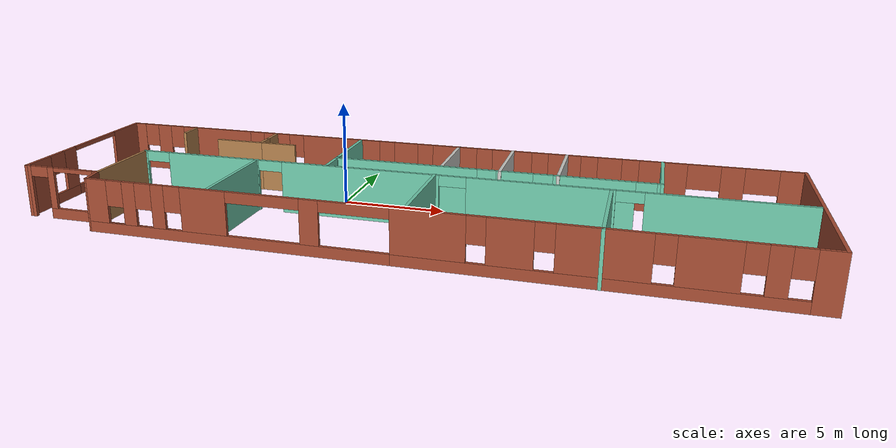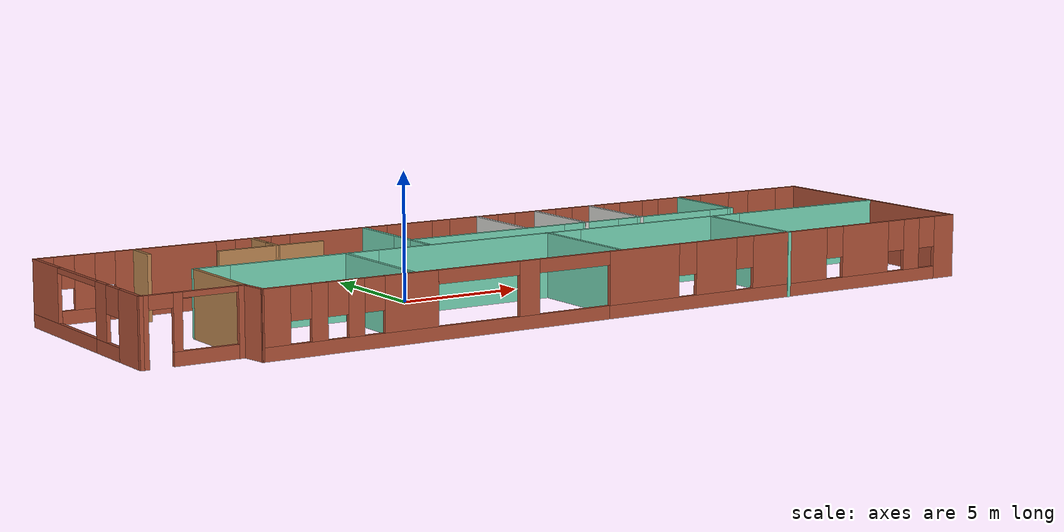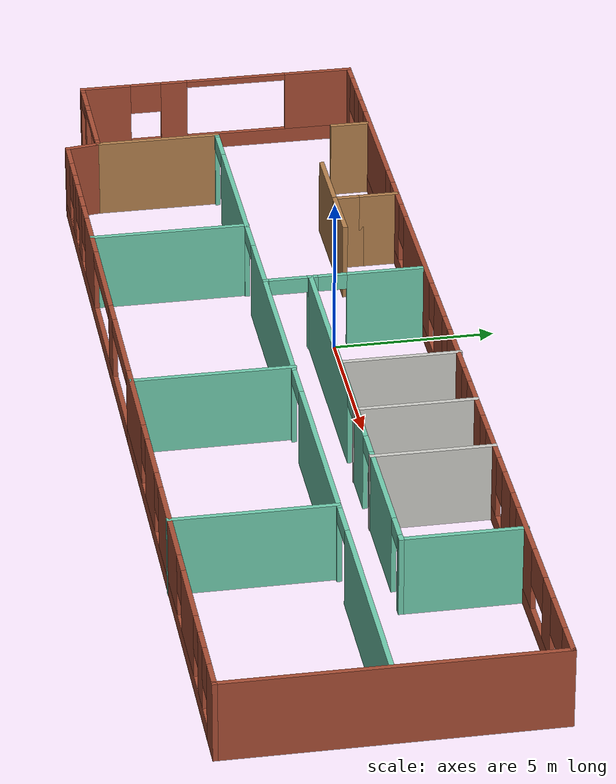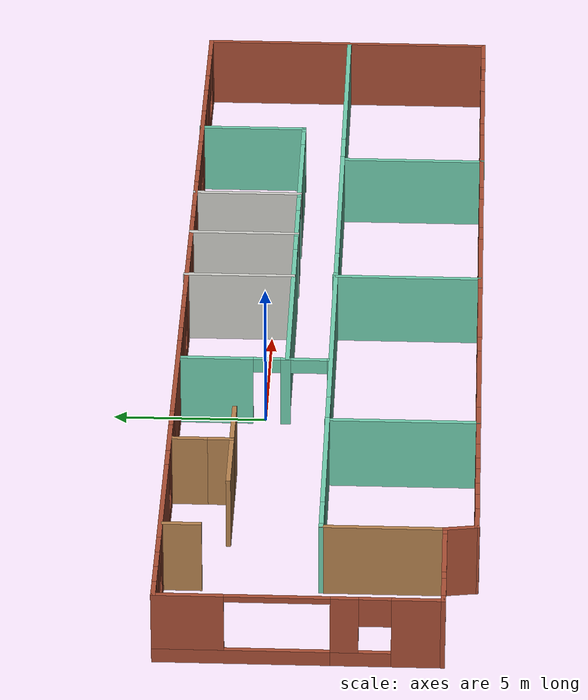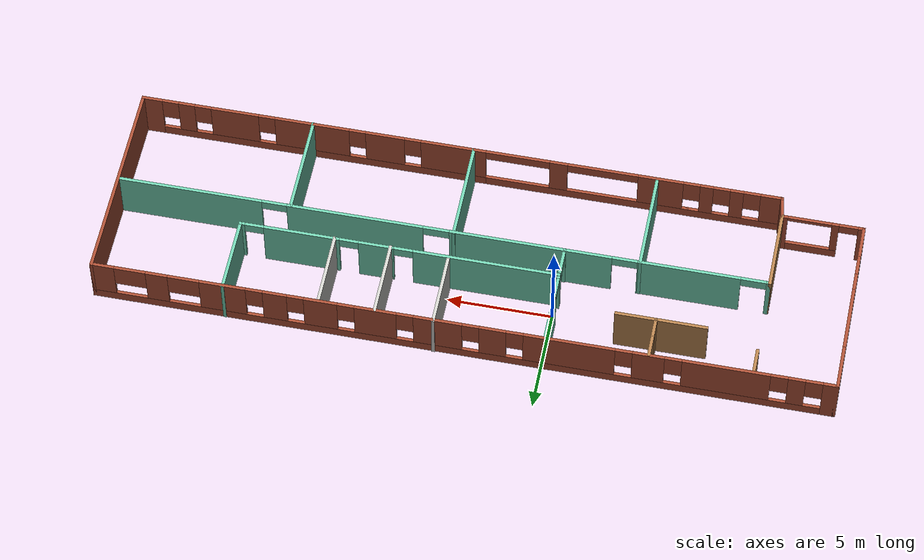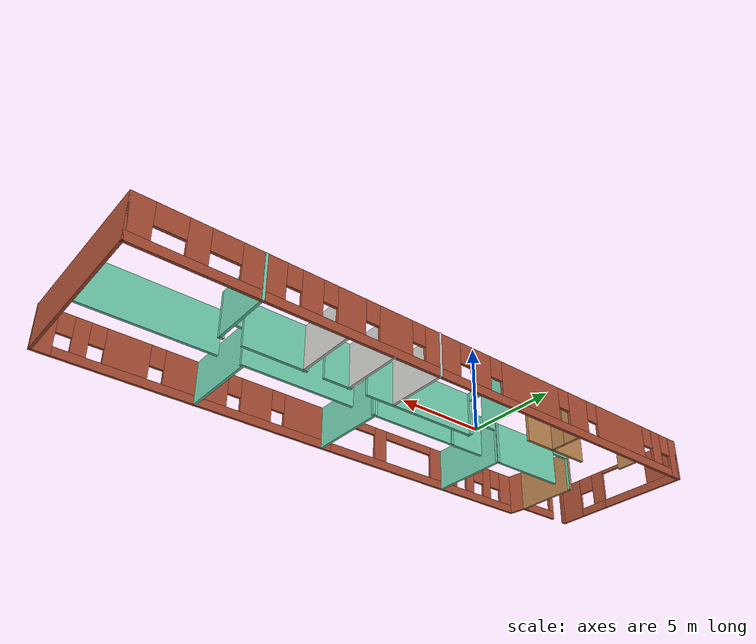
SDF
<?xml version='1.0'?>
<sdf version='1.6'>
  <model name='building_model'>
    <pose frame=''>3.8013 -2.05581 0 0 -0 0</pose>
    <link name='Wall_1'>
      <pose frame=''>-15.5 -3.93769 0 0 -0 3.14159</pose>
      <visual name='Wall_1_Visual_0'>
        <pose frame=''>-1.82542 0 1.25 0 -0 0</pose>
        <geometry>
          <box>
            <size>0.349165 0.15 2.5</size>
          </box>
        </geometry>
        <material>
          <script>
            <uri>file://media/materials/scripts/gazebo.material</uri>
            <name>Gazebo/Bricks</name>
          </script>
          <ambient>1 1 1 1</ambient>
        </material>
        <meta>
          <layer>0</layer>
        </meta>
      </visual>
      <collision name='Wall_1_Collision_0'>
        <geometry>
          <box>
            <size>0.349165 0.15 2.5</size>
          </box>
        </geometry>
        <pose frame=''>-1.82542 0 1.25 0 -0 0</pose>
      </collision>
      <visual name='Wall_1_Visual_1'>
        <pose frame=''>1.83136 0 1.25 0 -0 0</pose>
        <geometry>
          <box>
            <size>0.337283 0.15 2.5</size>
          </box>
        </geometry>
        <material>
          <script>
            <uri>file://media/materials/scripts/gazebo.material</uri>
            <name>Gazebo/Bricks</name>
          </script>
          <ambient>1 1 1 1</ambient>
        </material>
        <meta>
          <layer>0</layer>
        </meta>
      </visual>
      <collision name='Wall_1_Collision_1'>
        <geometry>
          <box>
            <size>0.337283 0.15 2.5</size>
          </box>
        </geometry>
        <pose frame=''>1.83136 0 1.25 0 -0 0</pose>
      </collision>
      <visual name='Wall_1_Visual_2'>
        <pose frame=''>-0.444059 0 0.25 0 -0 0</pose>
        <geometry>
          <box>
            <size>2.41355 0.15 0.5</size>
          </box>
        </geometry>
        <material>
          <script>
            <uri>file://media/materials/scripts/gazebo.material</uri>
            <name>Gazebo/Bricks</name>
          </script>
          <ambient>1 1 1 1</ambient>
        </material>
        <meta>
          <layer>0</layer>
        </meta>
      </visual>
      <collision name='Wall_1_Collision_2'>
        <geometry>
          <box>
            <size>2.41355 0.15 0.5</size>
          </box>
        </geometry>
        <pose frame=''>-0.444059 0 0.25 0 -0 0</pose>
      </collision>
      <visual name='Wall_1_Visual_3'>
        <pose frame=''>0.594441 0 1.5 0 -0 0</pose>
        <geometry>
          <box>
            <size>0.336552 0.15 2</size>
          </box>
        </geometry>
        <material>
          <script>
            <uri>file://media/materials/scripts/gazebo.material</uri>
            <name>Gazebo/Bricks</name>
          </script>
          <ambient>1 1 1 1</ambient>
        </material>
        <meta>
          <layer>0</layer>
        </meta>
      </visual>
      <collision name='Wall_1_Collision_3'>
        <geometry>
          <box>
            <size>0.336552 0.15 2</size>
          </box>
        </geometry>
        <pose frame=''>0.594441 0 1.5 0 -0 0</pose>
      </collision>
      <visual name='Wall_1_Visual_4'>
        <pose frame=''>1.21272 0 2.25 0 -0 0</pose>
        <geometry>
          <box>
            <size>0.9 0.15 0.5</size>
          </box>
        </geometry>
        <material>
          <script>
            <uri>file://media/materials/scripts/gazebo.material</uri>
            <name>Gazebo/Bricks</name>
          </script>
          <ambient>1 1 1 1</ambient>
        </material>
        <meta>
          <layer>0</layer>
        </meta>
      </visual>
      <collision name='Wall_1_Collision_4'>
        <geometry>
          <box>
            <size>0.9 0.15 0.5</size>
          </box>
        </geometry>
        <pose frame=''>1.21272 0 2.25 0 -0 0</pose>
      </collision>
      <visual name='Wall_1_Visual_5'>
        <pose frame=''>-0.612335 0 2.4 0 -0 0</pose>
        <geometry>
          <box>
            <size>2.077 0.15 0.2</size>
          </box>
        </geometry>
        <material>
          <script>
            <uri>file://media/materials/scripts/gazebo.material</uri>
            <name>Gazebo/Bricks</name>
          </script>
          <ambient>1 1 1 1</ambient>
        </material>
        <meta>
          <layer>0</layer>
        </meta>
      </visual>
      <collision name='Wall_1_Collision_5'>
        <geometry>
          <box>
            <size>2.077 0.15 0.2</size>
          </box>
        </geometry>
        <pose frame=''>-0.612335 0 2.4 0 -0 0</pose>
      </collision>
    </link>
    <link name='Wall_10'>
      <pose frame=''>1.85 -0.087691 0 0 -0 0</pose>
      <visual name='Wall_10_Visual_0'>
        <pose frame=''>-15.3838 0 1.25 0 -0 0</pose>
        <geometry>
          <box>
            <size>0.232456 0.15 2.5</size>
          </box>
        </geometry>
        <material>
          <script>
            <uri>file://media/materials/scripts/gazebo.material</uri>
            <name>Gazebo/Grey</name>
          </script>
          <ambient>0.435294 0.796078 0.67451 1</ambient>
        </material>
        <meta>
          <layer>0</layer>
        </meta>
      </visual>
      <collision name='Wall_10_Collision_0'>
        <geometry>
          <box>
            <size>0.232456 0.15 2.5</size>
          </box>
        </geometry>
        <pose frame=''>-15.3838 0 1.25 0 -0 0</pose>
      </collision>
      <visual name='Wall_10_Visual_1'>
        <pose frame=''>-11.6471 0 1.25 0 -0 0</pose>
        <geometry>
          <box>
            <size>4.84093 0.15 2.5</size>
          </box>
        </geometry>
        <material>
          <script>
            <uri>file://media/materials/scripts/gazebo.material</uri>
            <name>Gazebo/Grey</name>
          </script>
          <ambient>0.435294 0.796078 0.67451 1</ambient>
        </material>
        <meta>
          <layer>0</layer>
        </meta>
      </visual>
      <collision name='Wall_10_Collision_1'>
        <geometry>
          <box>
            <size>4.84093 0.15 2.5</size>
          </box>
        </geometry>
        <pose frame=''>-11.6471 0 1.25 0 -0 0</pose>
      </collision>
      <visual name='Wall_10_Visual_2'>
        <pose frame=''>-4.17733 0 1.25 0 -0 0</pose>
        <geometry>
          <box>
            <size>7.69857 0.15 2.5</size>
          </box>
        </geometry>
        <material>
          <script>
            <uri>file://media/materials/scripts/gazebo.material</uri>
            <name>Gazebo/Grey</name>
          </script>
          <ambient>0.435294 0.796078 0.67451 1</ambient>
        </material>
        <meta>
          <layer>0</layer>
        </meta>
      </visual>
      <collision name='Wall_10_Collision_2'>
        <geometry>
          <box>
            <size>7.69857 0.15 2.5</size>
          </box>
        </geometry>
        <pose frame=''>-4.17733 0 1.25 0 -0 0</pose>
      </collision>
      <visual name='Wall_10_Visual_3'>
        <pose frame=''>4.17858 0 1.25 0 -0 0</pose>
        <geometry>
          <box>
            <size>6.51326 0.15 2.5</size>
          </box>
        </geometry>
        <material>
          <script>
            <uri>file://media/materials/scripts/gazebo.material</uri>
            <name>Gazebo/Grey</name>
          </script>
          <ambient>0.435294 0.796078 0.67451 1</ambient>
        </material>
        <meta>
          <layer>0</layer>
        </meta>
      </visual>
      <collision name='Wall_10_Collision_3'>
        <geometry>
          <box>
            <size>6.51326 0.15 2.5</size>
          </box>
        </geometry>
        <pose frame=''>4.17858 0 1.25 0 -0 0</pose>
      </collision>
      <visual name='Wall_10_Visual_4'>
        <pose frame=''>12.0676 0 1.25 0 -0 0</pose>
        <geometry>
          <box>
            <size>6.86479 0.15 2.5</size>
          </box>
        </geometry>
        <material>
          <script>
            <uri>file://media/materials/scripts/gazebo.material</uri>
            <name>Gazebo/Grey</name>
          </script>
          <ambient>0.435294 0.796078 0.67451 1</ambient>
        </material>
        <meta>
          <layer>0</layer>
        </meta>
      </visual>
      <collision name='Wall_10_Collision_4'>
        <geometry>
          <box>
            <size>6.86479 0.15 2.5</size>
          </box>
        </geometry>
        <pose frame=''>12.0676 0 1.25 0 -0 0</pose>
      </collision>
      <visual name='Wall_10_Visual_5'>
        <pose frame=''>-14.6675 0 2.25 0 -0 0</pose>
        <geometry>
          <box>
            <size>1.2 0.15 0.5</size>
          </box>
        </geometry>
        <material>
          <script>
            <uri>file://media/materials/scripts/gazebo.material</uri>
            <name>Gazebo/Grey</name>
          </script>
          <ambient>0.435294 0.796078 0.67451 1</ambient>
        </material>
        <meta>
          <layer>0</layer>
        </meta>
      </visual>
      <collision name='Wall_10_Collision_5'>
        <geometry>
          <box>
            <size>1.2 0.15 0.5</size>
          </box>
        </geometry>
        <pose frame=''>-14.6675 0 2.25 0 -0 0</pose>
      </collision>
      <visual name='Wall_10_Visual_6'>
        <pose frame=''>-8.62661 0 2.25 0 -0 0</pose>
        <geometry>
          <box>
            <size>1.2 0.15 0.5</size>
          </box>
        </geometry>
        <material>
          <script>
            <uri>file://media/materials/scripts/gazebo.material</uri>
            <name>Gazebo/Grey</name>
          </script>
          <ambient>0.435294 0.796078 0.67451 1</ambient>
        </material>
        <meta>
          <layer>0</layer>
        </meta>
      </visual>
      <collision name='Wall_10_Collision_6'>
        <geometry>
          <box>
            <size>1.2 0.15 0.5</size>
          </box>
        </geometry>
        <pose frame=''>-8.62661 0 2.25 0 -0 0</pose>
      </collision>
      <visual name='Wall_10_Visual_7'>
        <pose frame=''>0.296954 0 2.25 0 -0 0</pose>
        <geometry>
          <box>
            <size>1.25 0.15 0.5</size>
          </box>
        </geometry>
        <material>
          <script>
            <uri>file://media/materials/scripts/gazebo.material</uri>
            <name>Gazebo/Grey</name>
          </script>
          <ambient>0.435294 0.796078 0.67451 1</ambient>
        </material>
        <meta>
          <layer>0</layer>
        </meta>
      </visual>
      <collision name='Wall_10_Collision_7'>
        <geometry>
          <box>
            <size>1.25 0.15 0.5</size>
          </box>
        </geometry>
        <pose frame=''>0.296954 0 2.25 0 -0 0</pose>
      </collision>
      <visual name='Wall_10_Visual_8'>
        <pose frame=''>8.03521 0 2.25 0 -0 0</pose>
        <geometry>
          <box>
            <size>1.2 0.15 0.5</size>
          </box>
        </geometry>
        <material>
          <script>
            <uri>file://media/materials/scripts/gazebo.material</uri>
            <name>Gazebo/Grey</name>
          </script>
          <ambient>0.435294 0.796078 0.67451 1</ambient>
        </material>
        <meta>
          <layer>0</layer>
        </meta>
      </visual>
      <collision name='Wall_10_Collision_8'>
        <geometry>
          <box>
            <size>1.2 0.15 0.5</size>
          </box>
        </geometry>
        <pose frame=''>8.03521 0 2.25 0 -0 0</pose>
      </collision>
    </link>
    <link name='Wall_12'>
      <collision name='Wall_12_Collision'>
        <geometry>
          <box>
            <size>1.25 0.15 2.5</size>
          </box>
        </geometry>
        <pose frame=''>0 0 1.25 0 -0 0</pose>
      </collision>
      <visual name='Wall_12_Visual'>
        <pose frame=''>0 0 1.25 0 -0 0</pose>
        <geometry>
          <box>
            <size>1.25 0.15 2.5</size>
          </box>
        </geometry>
        <material>
          <script>
            <uri>file://media/materials/scripts/gazebo.material</uri>
            <name>Gazebo/Wood</name>
          </script>
          <ambient>1 1 1 1</ambient>
        </material>
        <meta>
          <layer>0</layer>
        </meta>
      </visual>
      <pose frame=''>-13.575 4.25547 0 0 -0 1.5708</pose>
    </link>
    <link name='Wall_14'>
      <collision name='Wall_14_Collision'>
        <geometry>
          <box>
            <size>1.25 0.15 2.5</size>
          </box>
        </geometry>
        <pose frame=''>0 0 1.25 0 -0 0</pose>
      </collision>
      <visual name='Wall_14_Visual'>
        <pose frame=''>0 0 1.25 0 -0 0</pose>
        <geometry>
          <box>
            <size>1.25 0.15 2.5</size>
          </box>
        </geometry>
        <material>
          <script>
            <uri>file://media/materials/scripts/gazebo.material</uri>
            <name>Gazebo/Wood</name>
          </script>
          <ambient>1 1 1 1</ambient>
        </material>
        <meta>
          <layer>0</layer>
        </meta>
      </visual>
      <pose frame=''>-8.74774 4.32205 0 0 0 -1.5708</pose>
    </link>
    <link name='Wall_15'>
      <collision name='Wall_15_Collision'>
        <geometry>
          <box>
            <size>1 0.15 2.5</size>
          </box>
        </geometry>
        <pose frame=''>0 0 1.25 0 -0 0</pose>
      </collision>
      <visual name='Wall_15_Visual'>
        <pose frame=''>0 0 1.25 0 -0 0</pose>
        <geometry>
          <box>
            <size>1 0.15 2.5</size>
          </box>
        </geometry>
        <material>
          <script>
            <uri>file://media/materials/scripts/gazebo.material</uri>
            <name>Gazebo/Wood</name>
          </script>
          <ambient>1 1 1 1</ambient>
        </material>
        <meta>
          <layer>0</layer>
        </meta>
      </visual>
      <pose frame=''>-8.74774 3.34705 0 0 0 -1.5708</pose>
    </link>
    <link name='Wall_16'>
      <collision name='Wall_16_Collision'>
        <geometry>
          <box>
            <size>2.5 0.15 2.5</size>
          </box>
        </geometry>
        <pose frame=''>0 0 1.25 0 -0 0</pose>
      </collision>
      <visual name='Wall_16_Visual'>
        <pose frame=''>0 0 1.25 0 -0 0</pose>
        <geometry>
          <box>
            <size>2.5 0.15 2.5</size>
          </box>
        </geometry>
        <material>
          <script>
            <uri>file://media/materials/scripts/gazebo.material</uri>
            <name>Gazebo/Wood</name>
          </script>
          <ambient>1 1 1 1</ambient>
        </material>
        <meta>
          <layer>0</layer>
        </meta>
      </visual>
      <pose frame=''>-9.92274 2.92205 0 0 -0 3.14159</pose>
    </link>
    <link name='Wall_18'>
      <collision name='Wall_18_Collision'>
        <geometry>
          <box>
            <size>2 0.15 2.5</size>
          </box>
        </geometry>
        <pose frame=''>0 0 1.25 0 -0 0</pose>
      </collision>
      <visual name='Wall_18_Visual'>
        <pose frame=''>0 0 1.25 0 -0 0</pose>
        <geometry>
          <box>
            <size>2 0.15 2.5</size>
          </box>
        </geometry>
        <material>
          <script>
            <uri>file://media/materials/scripts/gazebo.material</uri>
            <name>Gazebo/Wood</name>
          </script>
          <ambient>1 1 1 1</ambient>
        </material>
        <meta>
          <layer>0</layer>
        </meta>
      </visual>
      <pose frame=''>-7.82274 2.92205 0 0 -0 0</pose>
    </link>
    <link name='Wall_20'>
      <pose frame=''>-3.9406 2.34911 0 0 -0 1.5708</pose>
      <visual name='Wall_20_Visual_0'>
        <pose frame=''>-2.41051 0 1.25 0 -0 0</pose>
        <geometry>
          <box>
            <size>0.178975 0.15 2.5</size>
          </box>
        </geometry>
        <material>
          <script>
            <uri>file://media/materials/scripts/gazebo.material</uri>
            <name>Gazebo/Grey</name>
          </script>
          <ambient>0.435294 0.796078 0.67451 1</ambient>
        </material>
        <meta>
          <layer>0</layer>
        </meta>
      </visual>
      <collision name='Wall_20_Collision_0'>
        <geometry>
          <box>
            <size>0.178975 0.15 2.5</size>
          </box>
        </geometry>
        <pose frame=''>-2.41051 0 1.25 0 -0 0</pose>
      </collision>
      <visual name='Wall_20_Visual_1'>
        <pose frame=''>-0.958717 0 1.25 0 -0 0</pose>
        <geometry>
          <box>
            <size>0.324616 0.15 2.5</size>
          </box>
        </geometry>
        <material>
          <script>
            <uri>file://media/materials/scripts/gazebo.material</uri>
            <name>Gazebo/Grey</name>
          </script>
          <ambient>0.435294 0.796078 0.67451 1</ambient>
        </material>
        <meta>
          <layer>0</layer>
        </meta>
      </visual>
      <collision name='Wall_20_Collision_1'>
        <geometry>
          <box>
            <size>0.324616 0.15 2.5</size>
          </box>
        </geometry>
        <pose frame=''>-0.958717 0 1.25 0 -0 0</pose>
      </collision>
      <visual name='Wall_20_Visual_2'>
        <pose frame=''>1.3018 0 1.25 0 -0 0</pose>
        <geometry>
          <box>
            <size>2.39641 0.15 2.5</size>
          </box>
        </geometry>
        <material>
          <script>
            <uri>file://media/materials/scripts/gazebo.material</uri>
            <name>Gazebo/Grey</name>
          </script>
          <ambient>0.435294 0.796078 0.67451 1</ambient>
        </material>
        <meta>
          <layer>0</layer>
        </meta>
      </visual>
      <collision name='Wall_20_Collision_2'>
        <geometry>
          <box>
            <size>2.39641 0.15 2.5</size>
          </box>
        </geometry>
        <pose frame=''>1.3018 0 1.25 0 -0 0</pose>
      </collision>
      <visual name='Wall_20_Visual_3'>
        <pose frame=''>-1.72103 0 2.25 0 -0 0</pose>
        <geometry>
          <box>
            <size>1.2 0.15 0.5</size>
          </box>
        </geometry>
        <material>
          <script>
            <uri>file://media/materials/scripts/gazebo.material</uri>
            <name>Gazebo/Grey</name>
          </script>
          <ambient>0.435294 0.796078 0.67451 1</ambient>
        </material>
        <meta>
          <layer>0</layer>
        </meta>
      </visual>
      <collision name='Wall_20_Collision_3'>
        <geometry>
          <box>
            <size>1.2 0.15 0.5</size>
          </box>
        </geometry>
        <pose frame=''>-1.72103 0 2.25 0 -0 0</pose>
      </collision>
      <visual name='Wall_20_Visual_4'>
        <pose frame=''>-0.346409 0 2.25 0 -0 0</pose>
        <geometry>
          <box>
            <size>0.9 0.15 0.5</size>
          </box>
        </geometry>
        <material>
          <script>
            <uri>file://media/materials/scripts/gazebo.material</uri>
            <name>Gazebo/Grey</name>
          </script>
          <ambient>0.435294 0.796078 0.67451 1</ambient>
        </material>
        <meta>
          <layer>0</layer>
        </meta>
      </visual>
      <collision name='Wall_20_Collision_4'>
        <geometry>
          <box>
            <size>0.9 0.15 0.5</size>
          </box>
        </geometry>
        <pose frame=''>-0.346409 0 2.25 0 -0 0</pose>
      </collision>
    </link>
    <link name='Wall_22'>
      <collision name='Wall_22_Collision'>
        <geometry>
          <box>
            <size>5 0.15 2.5</size>
          </box>
        </geometry>
        <pose frame=''>0 0 1.25 0 -0 0</pose>
      </collision>
      <visual name='Wall_22_Visual'>
        <pose frame=''>0 0 1.25 0 -0 0</pose>
        <geometry>
          <box>
            <size>5 0.15 2.5</size>
          </box>
        </geometry>
        <material>
          <script>
            <uri>file://media/materials/scripts/gazebo.material</uri>
            <name>Gazebo/Grey</name>
          </script>
          <ambient>0.435294 0.796078 0.67451 1</ambient>
        </material>
        <meta>
          <layer>0</layer>
        </meta>
      </visual>
      <pose frame=''>-7.5007 -2.50088 0 0 0 -1.5708</pose>
    </link>
    <link name='Wall_24'>
      <pose frame=''>3.62951 1.33207 0 0 -0 0</pose>
      <visual name='Wall_24_Visual_0'>
        <pose frame=''>-4.14379 0 1.25 0 -0 0</pose>
        <geometry>
          <box>
            <size>6.96242 0.15 2.5</size>
          </box>
        </geometry>
        <material>
          <script>
            <uri>file://media/materials/scripts/gazebo.material</uri>
            <name>Gazebo/Grey</name>
          </script>
          <ambient>0.435294 0.796078 0.67451 1</ambient>
        </material>
        <meta>
          <layer>0</layer>
        </meta>
      </visual>
      <collision name='Wall_24_Collision_0'>
        <geometry>
          <box>
            <size>6.96242 0.15 2.5</size>
          </box>
        </geometry>
        <pose frame=''>-4.14379 0 1.25 0 -0 0</pose>
      </collision>
      <visual name='Wall_24_Visual_1'>
        <pose frame=''>1.07877 0 1.25 0 -0 0</pose>
        <geometry>
          <box>
            <size>1.6827 0.15 2.5</size>
          </box>
        </geometry>
        <material>
          <script>
            <uri>file://media/materials/scripts/gazebo.material</uri>
            <name>Gazebo/Grey</name>
          </script>
          <ambient>0.435294 0.796078 0.67451 1</ambient>
        </material>
        <meta>
          <layer>0</layer>
        </meta>
      </visual>
      <collision name='Wall_24_Collision_1'>
        <geometry>
          <box>
            <size>1.6827 0.15 2.5</size>
          </box>
        </geometry>
        <pose frame=''>1.07877 0 1.25 0 -0 0</pose>
      </collision>
      <visual name='Wall_24_Visual_2'>
        <pose frame=''>4.62999 0 1.25 0 -0 0</pose>
        <geometry>
          <box>
            <size>3.61973 0.15 2.5</size>
          </box>
        </geometry>
        <material>
          <script>
            <uri>file://media/materials/scripts/gazebo.material</uri>
            <name>Gazebo/Grey</name>
          </script>
          <ambient>0.435294 0.796078 0.67451 1</ambient>
        </material>
        <meta>
          <layer>0</layer>
        </meta>
      </visual>
      <collision name='Wall_24_Collision_2'>
        <geometry>
          <box>
            <size>3.61973 0.15 2.5</size>
          </box>
        </geometry>
        <pose frame=''>4.62999 0 1.25 0 -0 0</pose>
      </collision>
      <visual name='Wall_24_Visual_3'>
        <pose frame=''>7.48243 0 1.25 0 -0 0</pose>
        <geometry>
          <box>
            <size>0.285144 0.15 2.5</size>
          </box>
        </geometry>
        <material>
          <script>
            <uri>file://media/materials/scripts/gazebo.material</uri>
            <name>Gazebo/Grey</name>
          </script>
          <ambient>0.435294 0.796078 0.67451 1</ambient>
        </material>
        <meta>
          <layer>0</layer>
        </meta>
      </visual>
      <collision name='Wall_24_Collision_3'>
        <geometry>
          <box>
            <size>0.285144 0.15 2.5</size>
          </box>
        </geometry>
        <pose frame=''>7.48243 0 1.25 0 -0 0</pose>
      </collision>
      <visual name='Wall_24_Visual_4'>
        <pose frame=''>-0.212578 0 2.25 0 -0 0</pose>
        <geometry>
          <box>
            <size>0.9 0.15 0.5</size>
          </box>
        </geometry>
        <material>
          <script>
            <uri>file://media/materials/scripts/gazebo.material</uri>
            <name>Gazebo/Grey</name>
          </script>
          <ambient>0.435294 0.796078 0.67451 1</ambient>
        </material>
        <meta>
          <layer>0</layer>
        </meta>
      </visual>
      <collision name='Wall_24_Collision_4'>
        <geometry>
          <box>
            <size>0.9 0.15 0.5</size>
          </box>
        </geometry>
        <pose frame=''>-0.212578 0 2.25 0 -0 0</pose>
      </collision>
      <visual name='Wall_24_Visual_5'>
        <pose frame=''>2.37012 0 2.25 0 -0 0</pose>
        <geometry>
          <box>
            <size>0.9 0.15 0.5</size>
          </box>
        </geometry>
        <material>
          <script>
            <uri>file://media/materials/scripts/gazebo.material</uri>
            <name>Gazebo/Grey</name>
          </script>
          <ambient>0.435294 0.796078 0.67451 1</ambient>
        </material>
        <meta>
          <layer>0</layer>
        </meta>
      </visual>
      <collision name='Wall_24_Collision_5'>
        <geometry>
          <box>
            <size>0.9 0.15 0.5</size>
          </box>
        </geometry>
        <pose frame=''>2.37012 0 2.25 0 -0 0</pose>
      </collision>
      <visual name='Wall_24_Visual_6'>
        <pose frame=''>6.88986 0 2.25 0 -0 0</pose>
        <geometry>
          <box>
            <size>0.9 0.15 0.5</size>
          </box>
        </geometry>
        <material>
          <script>
            <uri>file://media/materials/scripts/gazebo.material</uri>
            <name>Gazebo/Grey</name>
          </script>
          <ambient>0.435294 0.796078 0.67451 1</ambient>
        </material>
        <meta>
          <layer>0</layer>
        </meta>
      </visual>
      <collision name='Wall_24_Collision_6'>
        <geometry>
          <box>
            <size>0.9 0.15 0.5</size>
          </box>
        </geometry>
        <pose frame=''>6.88986 0 2.25 0 -0 0</pose>
      </collision>
    </link>
    <link name='Wall_25'>
      <collision name='Wall_25_Collision'>
        <geometry>
          <box>
            <size>3.75 0.15 2.5</size>
          </box>
        </geometry>
        <pose frame=''>0 0 1.25 0 -0 0</pose>
      </collision>
      <visual name='Wall_25_Visual'>
        <pose frame=''>0 0 1.25 0 -0 0</pose>
        <geometry>
          <box>
            <size>3.75 0.15 2.5</size>
          </box>
        </geometry>
        <material>
          <script>
            <uri>file://media/materials/scripts/gazebo.material</uri>
            <name>Gazebo/Grey</name>
          </script>
          <ambient>0.435294 0.796078 0.67451 1</ambient>
        </material>
        <meta>
          <layer>0</layer>
        </meta>
      </visual>
      <pose frame=''>11.1795 3.13206 0 0 -0 1.5708</pose>
    </link>
    <link name='Wall_27'>
      <collision name='Wall_27_Collision'>
        <geometry>
          <box>
            <size>3.75 0.15 2.5</size>
          </box>
        </geometry>
        <pose frame=''>0 0 1.25 0 -0 0</pose>
      </collision>
      <visual name='Wall_27_Visual'>
        <pose frame=''>0 0 1.25 0 -0 0</pose>
        <geometry>
          <box>
            <size>3.75 0.15 2.5</size>
          </box>
        </geometry>
        <material>
          <script>
            <uri>file://media/materials/scripts/gazebo.material</uri>
            <name>Gazebo/CeilingTiled</name>
          </script>
          <ambient>1 1 1 1</ambient>
        </material>
        <meta>
          <layer>0</layer>
        </meta>
      </visual>
      <pose frame=''>1.26882 3.15218 0 0 -0 1.5708</pose>
    </link>
    <link name='Wall_29'>
      <collision name='Wall_29_Collision'>
        <geometry>
          <box>
            <size>3.75 0.15 2.5</size>
          </box>
        </geometry>
        <pose frame=''>0 0 1.25 0 -0 0</pose>
      </collision>
      <visual name='Wall_29_Visual'>
        <pose frame=''>0 0 1.25 0 -0 0</pose>
        <geometry>
          <box>
            <size>3.75 0.15 2.5</size>
          </box>
        </geometry>
        <material>
          <script>
            <uri>file://media/materials/scripts/gazebo.material</uri>
            <name>Gazebo/CeilingTiled</name>
          </script>
          <ambient>1 1 1 1</ambient>
        </material>
        <meta>
          <layer>0</layer>
        </meta>
      </visual>
      <pose frame=''>6.67937 3.11195 0 0 -0 1.5708</pose>
    </link>
    <link name='Wall_31'>
      <collision name='Wall_31_Collision'>
        <geometry>
          <box>
            <size>3.75 0.15 2.5</size>
          </box>
        </geometry>
        <pose frame=''>0 0 1.25 0 -0 0</pose>
      </collision>
      <visual name='Wall_31_Visual'>
        <pose frame=''>0 0 1.25 0 -0 0</pose>
        <geometry>
          <box>
            <size>3.75 0.15 2.5</size>
          </box>
        </geometry>
        <material>
          <script>
            <uri>file://media/materials/scripts/gazebo.material</uri>
            <name>Gazebo/CeilingTiled</name>
          </script>
          <ambient>1 1 1 1</ambient>
        </material>
        <meta>
          <layer>0</layer>
        </meta>
      </visual>
      <pose frame=''>4.02438 3.11195 0 0 -0 1.5708</pose>
    </link>
    <link name='Wall_33'>
      <collision name='Wall_33_Collision'>
        <geometry>
          <box>
            <size>5 0.15 2.5</size>
          </box>
        </geometry>
        <pose frame=''>0 0 1.25 0 -0 0</pose>
      </collision>
      <visual name='Wall_33_Visual'>
        <pose frame=''>0 0 1.25 0 -0 0</pose>
        <geometry>
          <box>
            <size>5 0.15 2.5</size>
          </box>
        </geometry>
        <material>
          <script>
            <uri>file://media/materials/scripts/gazebo.material</uri>
            <name>Gazebo/Grey</name>
          </script>
          <ambient>0.435294 0.796078 0.67451 1</ambient>
        </material>
        <meta>
          <layer>0</layer>
        </meta>
      </visual>
      <pose frame=''>1.30855 -2.48092 0 0 0 -1.5708</pose>
    </link>
    <link name='Wall_35'>
      <collision name='Wall_35_Collision'>
        <geometry>
          <box>
            <size>5 0.15 2.5</size>
          </box>
        </geometry>
        <pose frame=''>0 0 1.25 0 -0 0</pose>
      </collision>
      <visual name='Wall_35_Visual'>
        <pose frame=''>0 0 1.25 0 -0 0</pose>
        <geometry>
          <box>
            <size>5 0.15 2.5</size>
          </box>
        </geometry>
        <material>
          <script>
            <uri>file://media/materials/scripts/gazebo.material</uri>
            <name>Gazebo/Grey</name>
          </script>
          <ambient>0.435294 0.796078 0.67451 1</ambient>
        </material>
        <meta>
          <layer>0</layer>
        </meta>
      </visual>
      <pose frame=''>9.10356 -2.52718 0 0 0 -1.5708</pose>
    </link>
    <link name='Wall_4'>
      <pose frame=''>-17.425 0.487309 0 0 -0 1.5708</pose>
      <visual name='Wall_4_Visual_0'>
        <pose frame=''>-3.67371 0 1.25 0 -0 0</pose>
        <geometry>
          <box>
            <size>1.65259 0.15 2.5</size>
          </box>
        </geometry>
        <material>
          <script>
            <uri>file://media/materials/scripts/gazebo.material</uri>
            <name>Gazebo/Bricks</name>
          </script>
          <ambient>1 1 1 1</ambient>
        </material>
        <meta>
          <layer>0</layer>
        </meta>
      </visual>
      <collision name='Wall_4_Collision_0'>
        <geometry>
          <box>
            <size>1.65259 0.15 2.5</size>
          </box>
        </geometry>
        <pose frame=''>-3.67371 0 1.25 0 -0 0</pose>
      </collision>
      <visual name='Wall_4_Visual_1'>
        <pose frame=''>-1.91303 0 0.25 0 -0 0</pose>
        <geometry>
          <box>
            <size>1.86877 0.15 0.5</size>
          </box>
        </geometry>
        <material>
          <script>
            <uri>file://media/materials/scripts/gazebo.material</uri>
            <name>Gazebo/Bricks</name>
          </script>
          <ambient>1 1 1 1</ambient>
        </material>
        <meta>
          <layer>0</layer>
        </meta>
      </visual>
      <collision name='Wall_4_Collision_1'>
        <geometry>
          <box>
            <size>1.86877 0.15 0.5</size>
          </box>
        </geometry>
        <pose frame=''>-1.91303 0 0.25 0 -0 0</pose>
      </collision>
      <visual name='Wall_4_Visual_2'>
        <pose frame=''>1.76068 0 0.25 0 -0 0</pose>
        <geometry>
          <box>
            <size>5.47864 0.15 0.5</size>
          </box>
        </geometry>
        <material>
          <script>
            <uri>file://media/materials/scripts/gazebo.material</uri>
            <name>Gazebo/Bricks</name>
          </script>
          <ambient>1 1 1 1</ambient>
        </material>
        <meta>
          <layer>0</layer>
        </meta>
      </visual>
      <collision name='Wall_4_Collision_2'>
        <geometry>
          <box>
            <size>5.47864 0.15 0.5</size>
          </box>
        </geometry>
        <pose frame=''>1.76068 0 0.25 0 -0 0</pose>
      </collision>
      <visual name='Wall_4_Visual_3'>
        <pose frame=''>3.38368 0 1.5 0 -0 0</pose>
        <geometry>
          <box>
            <size>2.23264 0.15 2</size>
          </box>
        </geometry>
        <material>
          <script>
            <uri>file://media/materials/scripts/gazebo.material</uri>
            <name>Gazebo/Bricks</name>
          </script>
          <ambient>1 1 1 1</ambient>
        </material>
        <meta>
          <layer>0</layer>
        </meta>
      </visual>
      <collision name='Wall_4_Collision_3'>
        <geometry>
          <box>
            <size>2.23264 0.15 2</size>
          </box>
        </geometry>
        <pose frame=''>3.38368 0 1.5 0 -0 0</pose>
      </collision>
      <visual name='Wall_4_Visual_4'>
        <pose frame=''>-1.41303 0 1.5 0 -0 0</pose>
        <geometry>
          <box>
            <size>0.86877 0.15 2</size>
          </box>
        </geometry>
        <material>
          <script>
            <uri>file://media/materials/scripts/gazebo.material</uri>
            <name>Gazebo/Bricks</name>
          </script>
          <ambient>1 1 1 1</ambient>
        </material>
        <meta>
          <layer>0</layer>
        </meta>
      </visual>
      <collision name='Wall_4_Collision_4'>
        <geometry>
          <box>
            <size>0.86877 0.15 2</size>
          </box>
        </geometry>
        <pose frame=''>-1.41303 0 1.5 0 -0 0</pose>
      </collision>
      <visual name='Wall_4_Visual_5'>
        <pose frame=''>-1.41303 0 1.5 0 -0 0</pose>
        <geometry>
          <box>
            <size>0.86877 0.15 2</size>
          </box>
        </geometry>
        <material>
          <script>
            <uri>file://media/materials/scripts/gazebo.material</uri>
            <name>Gazebo/Bricks</name>
          </script>
          <ambient>1 1 1 1</ambient>
        </material>
        <meta>
          <layer>0</layer>
        </meta>
      </visual>
      <collision name='Wall_4_Collision_5'>
        <geometry>
          <box>
            <size>0.86877 0.15 2</size>
          </box>
        </geometry>
        <pose frame=''>-1.41303 0 1.5 0 -0 0</pose>
      </collision>
      <visual name='Wall_4_Visual_6'>
        <pose frame=''>-2.34741 0 2 0 -0 0</pose>
        <geometry>
          <box>
            <size>1 0.15 1</size>
          </box>
        </geometry>
        <material>
          <script>
            <uri>file://media/materials/scripts/gazebo.material</uri>
            <name>Gazebo/Bricks</name>
          </script>
          <ambient>1 1 1 1</ambient>
        </material>
        <meta>
          <layer>0</layer>
        </meta>
      </visual>
      <collision name='Wall_4_Collision_6'>
        <geometry>
          <box>
            <size>1 0.15 1</size>
          </box>
        </geometry>
        <pose frame=''>-2.34741 0 2 0 -0 0</pose>
      </collision>
      <visual name='Wall_4_Visual_7'>
        <pose frame=''>0.644356 0 2.4 0 -0 0</pose>
        <geometry>
          <box>
            <size>3.246 0.15 0.2</size>
          </box>
        </geometry>
        <material>
          <script>
            <uri>file://media/materials/scripts/gazebo.material</uri>
            <name>Gazebo/Bricks</name>
          </script>
          <ambient>1 1 1 1</ambient>
        </material>
        <meta>
          <layer>0</layer>
        </meta>
      </visual>
      <collision name='Wall_4_Collision_7'>
        <geometry>
          <box>
            <size>3.246 0.15 0.2</size>
          </box>
        </geometry>
        <pose frame=''>0.644356 0 2.4 0 -0 0</pose>
      </collision>
      <visual name='Wall_4_Visual_8'>
        <pose frame=''>0.644356 0 2.4 0 -0 0</pose>
        <geometry>
          <box>
            <size>3.246 0.15 0.2</size>
          </box>
        </geometry>
        <material>
          <script>
            <uri>file://media/materials/scripts/gazebo.material</uri>
            <name>Gazebo/Bricks</name>
          </script>
          <ambient>1 1 1 1</ambient>
        </material>
        <meta>
          <layer>0</layer>
        </meta>
      </visual>
      <collision name='Wall_4_Collision_8'>
        <geometry>
          <box>
            <size>3.246 0.15 0.2</size>
          </box>
        </geometry>
        <pose frame=''>0.644356 0 2.4 0 -0 0</pose>
      </collision>
    </link>
    <link name='Wall_5'>
      <pose frame=''>0 4.91231 0 0 -0 0</pose>
      <visual name='Wall_5_Visual_0'>
        <pose frame=''>-17.1316 0 1.25 0 -0 0</pose>
        <geometry>
          <box>
            <size>0.736763 0.15 2.5</size>
          </box>
        </geometry>
        <material>
          <script>
            <uri>file://media/materials/scripts/gazebo.material</uri>
            <name>Gazebo/Bricks</name>
          </script>
          <ambient>1 1 1 1</ambient>
        </material>
        <meta>
          <layer>0</layer>
        </meta>
      </visual>
      <collision name='Wall_5_Collision_0'>
        <geometry>
          <box>
            <size>0.736763 0.15 2.5</size>
          </box>
        </geometry>
        <pose frame=''>-17.1316 0 1.25 0 -0 0</pose>
      </collision>
      <visual name='Wall_5_Visual_1'>
        <pose frame=''>0.368382 0 0.25 0 -0 0</pose>
        <geometry>
          <box>
            <size>34.2632 0.15 0.5</size>
          </box>
        </geometry>
        <material>
          <script>
            <uri>file://media/materials/scripts/gazebo.material</uri>
            <name>Gazebo/Bricks</name>
          </script>
          <ambient>1 1 1 1</ambient>
        </material>
        <meta>
          <layer>0</layer>
        </meta>
      </visual>
      <collision name='Wall_5_Collision_1'>
        <geometry>
          <box>
            <size>34.2632 0.15 0.5</size>
          </box>
        </geometry>
        <pose frame=''>0.368382 0 0.25 0 -0 0</pose>
      </collision>
      <visual name='Wall_5_Visual_2'>
        <pose frame=''>-15.5652 0 1.5 0 -0 0</pose>
        <geometry>
          <box>
            <size>0.796011 0.15 2</size>
          </box>
        </geometry>
        <material>
          <script>
            <uri>file://media/materials/scripts/gazebo.material</uri>
            <name>Gazebo/Bricks</name>
          </script>
          <ambient>1 1 1 1</ambient>
        </material>
        <meta>
          <layer>0</layer>
        </meta>
      </visual>
      <collision name='Wall_5_Collision_2'>
        <geometry>
          <box>
            <size>0.796011 0.15 2</size>
          </box>
        </geometry>
        <pose frame=''>-15.5652 0 1.5 0 -0 0</pose>
      </collision>
      <visual name='Wall_5_Visual_3'>
        <pose frame=''>-12.3269 0 1.5 0 -0 0</pose>
        <geometry>
          <box>
            <size>4.08056 0.15 2</size>
          </box>
        </geometry>
        <material>
          <script>
            <uri>file://media/materials/scripts/gazebo.material</uri>
            <name>Gazebo/Bricks</name>
          </script>
          <ambient>1 1 1 1</ambient>
        </material>
        <meta>
          <layer>0</layer>
        </meta>
      </visual>
      <collision name='Wall_5_Collision_3'>
        <geometry>
          <box>
            <size>4.08056 0.15 2</size>
          </box>
        </geometry>
        <pose frame=''>-12.3269 0 1.5 0 -0 0</pose>
      </collision>
      <visual name='Wall_5_Visual_4'>
        <pose frame=''>-8.7417 0 1.5 0 -0 0</pose>
        <geometry>
          <box>
            <size>1.48993 0.15 2</size>
          </box>
        </geometry>
        <material>
          <script>
            <uri>file://media/materials/scripts/gazebo.material</uri>
            <name>Gazebo/Bricks</name>
          </script>
          <ambient>1 1 1 1</ambient>
        </material>
        <meta>
          <layer>0</layer>
        </meta>
      </visual>
      <collision name='Wall_5_Collision_4'>
        <geometry>
          <box>
            <size>1.48993 0.15 2</size>
          </box>
        </geometry>
        <pose frame=''>-8.7417 0 1.5 0 -0 0</pose>
      </collision>
      <visual name='Wall_5_Visual_5'>
        <pose frame=''>-5.06393 0 1.5 0 -0 0</pose>
        <geometry>
          <box>
            <size>4.2656 0.15 2</size>
          </box>
        </geometry>
        <material>
          <script>
            <uri>file://media/materials/scripts/gazebo.material</uri>
            <name>Gazebo/Bricks</name>
          </script>
          <ambient>1 1 1 1</ambient>
        </material>
        <meta>
          <layer>0</layer>
        </meta>
      </visual>
      <collision name='Wall_5_Collision_5'>
        <geometry>
          <box>
            <size>4.2656 0.15 2</size>
          </box>
        </geometry>
        <pose frame=''>-5.06393 0 1.5 0 -0 0</pose>
      </collision>
      <visual name='Wall_5_Visual_6'>
        <pose frame=''>-1.50182 0 1.5 0 -0 0</pose>
        <geometry>
          <box>
            <size>1.25862 0.15 2</size>
          </box>
        </geometry>
        <material>
          <script>
            <uri>file://media/materials/scripts/gazebo.material</uri>
            <name>Gazebo/Bricks</name>
          </script>
          <ambient>1 1 1 1</ambient>
        </material>
        <meta>
          <layer>0</layer>
        </meta>
      </visual>
      <collision name='Wall_5_Collision_6'>
        <geometry>
          <box>
            <size>1.25862 0.15 2</size>
          </box>
        </geometry>
        <pose frame=''>-1.50182 0 1.5 0 -0 0</pose>
      </collision>
      <visual name='Wall_5_Visual_7'>
        <pose frame=''>1.06568 0 1.5 0 -0 0</pose>
        <geometry>
          <box>
            <size>2.27637 0.15 2</size>
          </box>
        </geometry>
        <material>
          <script>
            <uri>file://media/materials/scripts/gazebo.material</uri>
            <name>Gazebo/Bricks</name>
          </script>
          <ambient>1 1 1 1</ambient>
        </material>
        <meta>
          <layer>0</layer>
        </meta>
      </visual>
      <collision name='Wall_5_Collision_7'>
        <geometry>
          <box>
            <size>2.27637 0.15 2</size>
          </box>
        </geometry>
        <pose frame=''>1.06568 0 1.5 0 -0 0</pose>
      </collision>
      <visual name='Wall_5_Visual_8'>
        <pose frame=''>3.9917 0 1.5 0 -0 0</pose>
        <geometry>
          <box>
            <size>1.97567 0.15 2</size>
          </box>
        </geometry>
        <material>
          <script>
            <uri>file://media/materials/scripts/gazebo.material</uri>
            <name>Gazebo/Bricks</name>
          </script>
          <ambient>1 1 1 1</ambient>
        </material>
        <meta>
          <layer>0</layer>
        </meta>
      </visual>
      <collision name='Wall_5_Collision_8'>
        <geometry>
          <box>
            <size>1.97567 0.15 2</size>
          </box>
        </geometry>
        <pose frame=''>3.9917 0 1.5 0 -0 0</pose>
      </collision>
      <visual name='Wall_5_Visual_9'>
        <pose frame=''>6.57076 0 1.5 0 -0 0</pose>
        <geometry>
          <box>
            <size>1.58245 0.15 2</size>
          </box>
        </geometry>
        <material>
          <script>
            <uri>file://media/materials/scripts/gazebo.material</uri>
            <name>Gazebo/Bricks</name>
          </script>
          <ambient>1 1 1 1</ambient>
        </material>
        <meta>
          <layer>0</layer>
        </meta>
      </visual>
      <collision name='Wall_5_Collision_9'>
        <geometry>
          <box>
            <size>1.58245 0.15 2</size>
          </box>
        </geometry>
        <pose frame=''>6.57076 0 1.5 0 -0 0</pose>
      </collision>
      <visual name='Wall_5_Visual_10'>
        <pose frame=''>8.73347 0 1.5 0 -0 0</pose>
        <geometry>
          <box>
            <size>1.14297 0.15 2</size>
          </box>
        </geometry>
        <material>
          <script>
            <uri>file://media/materials/scripts/gazebo.material</uri>
            <name>Gazebo/Bricks</name>
          </script>
          <ambient>1 1 1 1</ambient>
        </material>
        <meta>
          <layer>0</layer>
        </meta>
      </visual>
      <collision name='Wall_5_Collision_10'>
        <geometry>
          <box>
            <size>1.14297 0.15 2</size>
          </box>
        </geometry>
        <pose frame=''>8.73347 0 1.5 0 -0 0</pose>
      </collision>
      <visual name='Wall_5_Visual_11'>
        <pose frame=''>11.2069 0 1.5 0 -0 0</pose>
        <geometry>
          <box>
            <size>2.20394 0.15 2</size>
          </box>
        </geometry>
        <material>
          <script>
            <uri>file://media/materials/scripts/gazebo.material</uri>
            <name>Gazebo/Bricks</name>
          </script>
          <ambient>1 1 1 1</ambient>
        </material>
        <meta>
          <layer>0</layer>
        </meta>
      </visual>
      <collision name='Wall_5_Collision_11'>
        <geometry>
          <box>
            <size>2.20394 0.15 2</size>
          </box>
        </geometry>
        <pose frame=''>11.2069 0 1.5 0 -0 0</pose>
      </collision>
      <visual name='Wall_5_Visual_12'>
        <pose frame=''>14.3311 0 1.5 0 -0 0</pose>
        <geometry>
          <box>
            <size>1.04437 0.15 2</size>
          </box>
        </geometry>
        <material>
          <script>
            <uri>file://media/materials/scripts/gazebo.material</uri>
            <name>Gazebo/Bricks</name>
          </script>
          <ambient>1 1 1 1</ambient>
        </material>
        <meta>
          <layer>0</layer>
        </meta>
      </visual>
      <collision name='Wall_5_Collision_12'>
        <geometry>
          <box>
            <size>1.04437 0.15 2</size>
          </box>
        </geometry>
        <pose frame=''>14.3311 0 1.5 0 -0 0</pose>
      </collision>
      <visual name='Wall_5_Visual_13'>
        <pose frame=''>16.9266 0 1.5 0 -0 0</pose>
        <geometry>
          <box>
            <size>1.14674 0.15 2</size>
          </box>
        </geometry>
        <material>
          <script>
            <uri>file://media/materials/scripts/gazebo.material</uri>
            <name>Gazebo/Bricks</name>
          </script>
          <ambient>1 1 1 1</ambient>
        </material>
        <meta>
          <layer>0</layer>
        </meta>
      </visual>
      <collision name='Wall_5_Collision_13'>
        <geometry>
          <box>
            <size>1.14674 0.15 2</size>
          </box>
        </geometry>
        <pose frame=''>16.9266 0 1.5 0 -0 0</pose>
      </collision>
      <visual name='Wall_5_Visual_14'>
        <pose frame=''>-16.3632 0 1.9 0 -0 0</pose>
        <geometry>
          <box>
            <size>0.8 0.15 1.2</size>
          </box>
        </geometry>
        <material>
          <script>
            <uri>file://media/materials/scripts/gazebo.material</uri>
            <name>Gazebo/Bricks</name>
          </script>
          <ambient>1 1 1 1</ambient>
        </material>
        <meta>
          <layer>0</layer>
        </meta>
      </visual>
      <collision name='Wall_5_Collision_14'>
        <geometry>
          <box>
            <size>0.8 0.15 1.2</size>
          </box>
        </geometry>
        <pose frame=''>-16.3632 0 1.9 0 -0 0</pose>
      </collision>
      <visual name='Wall_5_Visual_15'>
        <pose frame=''>-14.7672 0 1.9 0 -0 0</pose>
        <geometry>
          <box>
            <size>0.8 0.15 1.2</size>
          </box>
        </geometry>
        <material>
          <script>
            <uri>file://media/materials/scripts/gazebo.material</uri>
            <name>Gazebo/Bricks</name>
          </script>
          <ambient>1 1 1 1</ambient>
        </material>
        <meta>
          <layer>0</layer>
        </meta>
      </visual>
      <collision name='Wall_5_Collision_15'>
        <geometry>
          <box>
            <size>0.8 0.15 1.2</size>
          </box>
        </geometry>
        <pose frame=''>-14.7672 0 1.9 0 -0 0</pose>
      </collision>
      <visual name='Wall_5_Visual_16'>
        <pose frame=''>-9.88667 0 1.9 0 -0 0</pose>
        <geometry>
          <box>
            <size>0.8 0.15 1.2</size>
          </box>
        </geometry>
        <material>
          <script>
            <uri>file://media/materials/scripts/gazebo.material</uri>
            <name>Gazebo/Bricks</name>
          </script>
          <ambient>1 1 1 1</ambient>
        </material>
        <meta>
          <layer>0</layer>
        </meta>
      </visual>
      <collision name='Wall_5_Collision_16'>
        <geometry>
          <box>
            <size>0.8 0.15 1.2</size>
          </box>
        </geometry>
        <pose frame=''>-9.88667 0 1.9 0 -0 0</pose>
      </collision>
      <visual name='Wall_5_Visual_17'>
        <pose frame=''>-7.59674 0 1.9 0 -0 0</pose>
        <geometry>
          <box>
            <size>0.8 0.15 1.2</size>
          </box>
        </geometry>
        <material>
          <script>
            <uri>file://media/materials/scripts/gazebo.material</uri>
            <name>Gazebo/Bricks</name>
          </script>
          <ambient>1 1 1 1</ambient>
        </material>
        <meta>
          <layer>0</layer>
        </meta>
      </visual>
      <collision name='Wall_5_Collision_17'>
        <geometry>
          <box>
            <size>0.8 0.15 1.2</size>
          </box>
        </geometry>
        <pose frame=''>-7.59674 0 1.9 0 -0 0</pose>
      </collision>
      <visual name='Wall_5_Visual_18'>
        <pose frame=''>-2.53113 0 1.9 0 -0 0</pose>
        <geometry>
          <box>
            <size>0.8 0.15 1.2</size>
          </box>
        </geometry>
        <material>
          <script>
            <uri>file://media/materials/scripts/gazebo.material</uri>
            <name>Gazebo/Bricks</name>
          </script>
          <ambient>1 1 1 1</ambient>
        </material>
        <meta>
          <layer>0</layer>
        </meta>
      </visual>
      <collision name='Wall_5_Collision_18'>
        <geometry>
          <box>
            <size>0.8 0.15 1.2</size>
          </box>
        </geometry>
        <pose frame=''>-2.53113 0 1.9 0 -0 0</pose>
      </collision>
      <visual name='Wall_5_Visual_19'>
        <pose frame=''>-0.47251 0 1.9 0 -0 0</pose>
        <geometry>
          <box>
            <size>0.8 0.15 1.2</size>
          </box>
        </geometry>
        <material>
          <script>
            <uri>file://media/materials/scripts/gazebo.material</uri>
            <name>Gazebo/Bricks</name>
          </script>
          <ambient>1 1 1 1</ambient>
        </material>
        <meta>
          <layer>0</layer>
        </meta>
      </visual>
      <collision name='Wall_5_Collision_19'>
        <geometry>
          <box>
            <size>0.8 0.15 1.2</size>
          </box>
        </geometry>
        <pose frame=''>-0.47251 0 1.9 0 -0 0</pose>
      </collision>
      <visual name='Wall_5_Visual_20'>
        <pose frame=''>2.60386 0 1.9 0 -0 0</pose>
        <geometry>
          <box>
            <size>0.8 0.15 1.2</size>
          </box>
        </geometry>
        <material>
          <script>
            <uri>file://media/materials/scripts/gazebo.material</uri>
            <name>Gazebo/Bricks</name>
          </script>
          <ambient>1 1 1 1</ambient>
        </material>
        <meta>
          <layer>0</layer>
        </meta>
      </visual>
      <collision name='Wall_5_Collision_20'>
        <geometry>
          <box>
            <size>0.8 0.15 1.2</size>
          </box>
        </geometry>
        <pose frame=''>2.60386 0 1.9 0 -0 0</pose>
      </collision>
      <visual name='Wall_5_Visual_21'>
        <pose frame=''>5.37953 0 1.9 0 -0 0</pose>
        <geometry>
          <box>
            <size>0.8 0.15 1.2</size>
          </box>
        </geometry>
        <material>
          <script>
            <uri>file://media/materials/scripts/gazebo.material</uri>
            <name>Gazebo/Bricks</name>
          </script>
          <ambient>1 1 1 1</ambient>
        </material>
        <meta>
          <layer>0</layer>
        </meta>
      </visual>
      <collision name='Wall_5_Collision_21'>
        <geometry>
          <box>
            <size>0.8 0.15 1.2</size>
          </box>
        </geometry>
        <pose frame=''>5.37953 0 1.9 0 -0 0</pose>
      </collision>
      <visual name='Wall_5_Visual_22'>
        <pose frame=''>7.76199 0 1.9 0 -0 0</pose>
        <geometry>
          <box>
            <size>0.8 0.15 1.2</size>
          </box>
        </geometry>
        <material>
          <script>
            <uri>file://media/materials/scripts/gazebo.material</uri>
            <name>Gazebo/Bricks</name>
          </script>
          <ambient>1 1 1 1</ambient>
        </material>
        <meta>
          <layer>0</layer>
        </meta>
      </visual>
      <collision name='Wall_5_Collision_22'>
        <geometry>
          <box>
            <size>0.8 0.15 1.2</size>
          </box>
        </geometry>
        <pose frame=''>7.76199 0 1.9 0 -0 0</pose>
      </collision>
      <visual name='Wall_5_Visual_23'>
        <pose frame=''>9.70496 0 1.9 0 -0 0</pose>
        <geometry>
          <box>
            <size>0.8 0.15 1.2</size>
          </box>
        </geometry>
        <material>
          <script>
            <uri>file://media/materials/scripts/gazebo.material</uri>
            <name>Gazebo/Bricks</name>
          </script>
          <ambient>1 1 1 1</ambient>
        </material>
        <meta>
          <layer>0</layer>
        </meta>
      </visual>
      <collision name='Wall_5_Collision_23'>
        <geometry>
          <box>
            <size>0.8 0.15 1.2</size>
          </box>
        </geometry>
        <pose frame=''>9.70496 0 1.9 0 -0 0</pose>
      </collision>
      <visual name='Wall_5_Visual_24'>
        <pose frame=''>13.0589 0 1.9 0 -0 0</pose>
        <geometry>
          <box>
            <size>1.5 0.15 1.2</size>
          </box>
        </geometry>
        <material>
          <script>
            <uri>file://media/materials/scripts/gazebo.material</uri>
            <name>Gazebo/Bricks</name>
          </script>
          <ambient>1 1 1 1</ambient>
        </material>
        <meta>
          <layer>0</layer>
        </meta>
      </visual>
      <collision name='Wall_5_Collision_24'>
        <geometry>
          <box>
            <size>1.5 0.15 1.2</size>
          </box>
        </geometry>
        <pose frame=''>13.0589 0 1.9 0 -0 0</pose>
      </collision>
      <visual name='Wall_5_Visual_25'>
        <pose frame=''>15.6033 0 1.9 0 -0 0</pose>
        <geometry>
          <box>
            <size>1.5 0.15 1.2</size>
          </box>
        </geometry>
        <material>
          <script>
            <uri>file://media/materials/scripts/gazebo.material</uri>
            <name>Gazebo/Bricks</name>
          </script>
          <ambient>1 1 1 1</ambient>
        </material>
        <meta>
          <layer>0</layer>
        </meta>
      </visual>
      <collision name='Wall_5_Collision_25'>
        <geometry>
          <box>
            <size>1.5 0.15 1.2</size>
          </box>
        </geometry>
        <pose frame=''>15.6033 0 1.9 0 -0 0</pose>
      </collision>
    </link>
    <link name='Wall_6'>
      <collision name='Wall_6_Collision'>
        <geometry>
          <box>
            <size>10 0.15 2.5</size>
          </box>
        </geometry>
        <pose frame=''>0 0 1.25 0 -0 0</pose>
      </collision>
      <visual name='Wall_6_Visual'>
        <pose frame=''>0 0 1.25 0 -0 0</pose>
        <geometry>
          <box>
            <size>10 0.15 2.5</size>
          </box>
        </geometry>
        <material>
          <script>
            <uri>file://media/materials/scripts/gazebo.material</uri>
            <name>Gazebo/Bricks</name>
          </script>
          <ambient>1 1 1 1</ambient>
        </material>
        <meta>
          <layer>0</layer>
        </meta>
      </visual>
      <pose frame=''>17.425 -0.012691 0 0 0 -1.5708</pose>
    </link>
    <link name='Wall_7'>
      <pose frame=''>2 -4.93769 0 0 -0 3.14159</pose>
      <visual name='Wall_7_Visual_0'>
        <pose frame=''>-14.9945 0 1.25 0 -0 0</pose>
        <geometry>
          <box>
            <size>1.011 0.15 2.5</size>
          </box>
        </geometry>
        <material>
          <script>
            <uri>file://media/materials/scripts/gazebo.material</uri>
            <name>Gazebo/Bricks</name>
          </script>
          <ambient>1 1 1 1</ambient>
        </material>
        <meta>
          <layer>0</layer>
        </meta>
      </visual>
      <collision name='Wall_7_Collision_0'>
        <geometry>
          <box>
            <size>1.011 0.15 2.5</size>
          </box>
        </geometry>
        <pose frame=''>-14.9945 0 1.25 0 -0 0</pose>
      </collision>
      <visual name='Wall_7_Visual_1'>
        <pose frame=''>-6.60655 0 0.25 0 -0 0</pose>
        <geometry>
          <box>
            <size>15.7649 0.15 0.5</size>
          </box>
        </geometry>
        <material>
          <script>
            <uri>file://media/materials/scripts/gazebo.material</uri>
            <name>Gazebo/Bricks</name>
          </script>
          <ambient>1 1 1 1</ambient>
        </material>
        <meta>
          <layer>0</layer>
        </meta>
      </visual>
      <collision name='Wall_7_Collision_1'>
        <geometry>
          <box>
            <size>15.7649 0.15 0.5</size>
          </box>
        </geometry>
        <pose frame=''>-6.60655 0 0.25 0 -0 0</pose>
      </collision>
      <visual name='Wall_7_Visual_2'>
        <pose frame=''>8.38795 0 0.25 0 -0 0</pose>
        <geometry>
          <box>
            <size>14.2241 0.15 0.5</size>
          </box>
        </geometry>
        <material>
          <script>
            <uri>file://media/materials/scripts/gazebo.material</uri>
            <name>Gazebo/Bricks</name>
          </script>
          <ambient>1 1 1 1</ambient>
        </material>
        <meta>
          <layer>0</layer>
        </meta>
      </visual>
      <collision name='Wall_7_Collision_2'>
        <geometry>
          <box>
            <size>14.2241 0.15 0.5</size>
          </box>
        </geometry>
        <pose frame=''>8.38795 0 0.25 0 -0 0</pose>
      </collision>
      <visual name='Wall_7_Visual_3'>
        <pose frame=''>4.7796 0 1.5 0 -0 0</pose>
        <geometry>
          <box>
            <size>0.856246 0.15 2</size>
          </box>
        </geometry>
        <material>
          <script>
            <uri>file://media/materials/scripts/gazebo.material</uri>
            <name>Gazebo/Bricks</name>
          </script>
          <ambient>1 1 1 1</ambient>
        </material>
        <meta>
          <layer>0</layer>
        </meta>
      </visual>
      <collision name='Wall_7_Collision_3'>
        <geometry>
          <box>
            <size>0.856246 0.15 2</size>
          </box>
        </geometry>
        <pose frame=''>4.7796 0 1.5 0 -0 0</pose>
      </collision>
      <visual name='Wall_7_Visual_4'>
        <pose frame=''>9.66524 0 1.5 0 -0 0</pose>
        <geometry>
          <box>
            <size>2.1625 0.15 2</size>
          </box>
        </geometry>
        <material>
          <script>
            <uri>file://media/materials/scripts/gazebo.material</uri>
            <name>Gazebo/Bricks</name>
          </script>
          <ambient>1 1 1 1</ambient>
        </material>
        <meta>
          <layer>0</layer>
        </meta>
      </visual>
      <collision name='Wall_7_Collision_4'>
        <geometry>
          <box>
            <size>2.1625 0.15 2</size>
          </box>
        </geometry>
        <pose frame=''>9.66524 0 1.5 0 -0 0</pose>
      </collision>
      <visual name='Wall_7_Visual_5'>
        <pose frame=''>11.8635 0 1.5 0 -0 0</pose>
        <geometry>
          <box>
            <size>0.634098 0.15 2</size>
          </box>
        </geometry>
        <material>
          <script>
            <uri>file://media/materials/scripts/gazebo.material</uri>
            <name>Gazebo/Bricks</name>
          </script>
          <ambient>1 1 1 1</ambient>
        </material>
        <meta>
          <layer>0</layer>
        </meta>
      </visual>
      <collision name='Wall_7_Collision_5'>
        <geometry>
          <box>
            <size>0.634098 0.15 2</size>
          </box>
        </geometry>
        <pose frame=''>11.8635 0 1.5 0 -0 0</pose>
      </collision>
      <visual name='Wall_7_Visual_6'>
        <pose frame=''>13.2976 0 1.5 0 -0 0</pose>
        <geometry>
          <box>
            <size>0.634098 0.15 2</size>
          </box>
        </geometry>
        <material>
          <script>
            <uri>file://media/materials/scripts/gazebo.material</uri>
            <name>Gazebo/Bricks</name>
          </script>
          <ambient>1 1 1 1</ambient>
        </material>
        <meta>
          <layer>0</layer>
        </meta>
      </visual>
      <collision name='Wall_7_Collision_6'>
        <geometry>
          <box>
            <size>0.634098 0.15 2</size>
          </box>
        </geometry>
        <pose frame=''>13.2976 0 1.5 0 -0 0</pose>
      </collision>
      <visual name='Wall_7_Visual_7'>
        <pose frame=''>14.9573 0 1.5 0 -0 0</pose>
        <geometry>
          <box>
            <size>1.08532 0.15 2</size>
          </box>
        </geometry>
        <material>
          <script>
            <uri>file://media/materials/scripts/gazebo.material</uri>
            <name>Gazebo/Bricks</name>
          </script>
          <ambient>1 1 1 1</ambient>
        </material>
        <meta>
          <layer>0</layer>
        </meta>
      </visual>
      <collision name='Wall_7_Collision_7'>
        <geometry>
          <box>
            <size>1.08532 0.15 2</size>
          </box>
        </geometry>
        <pose frame=''>14.9573 0 1.5 0 -0 0</pose>
      </collision>
      <visual name='Wall_7_Visual_8'>
        <pose frame=''>11.1465 0 0.5 0 -0 0</pose>
        <geometry>
          <box>
            <size>0.8 0.15 0</size>
          </box>
        </geometry>
        <material>
          <script>
            <uri>file://media/materials/scripts/gazebo.material</uri>
            <name>Gazebo/Bricks</name>
          </script>
          <ambient>1 1 1 1</ambient>
        </material>
        <meta>
          <layer>0</layer>
        </meta>
      </visual>
      <collision name='Wall_7_Collision_8'>
        <geometry>
          <box>
            <size>0.8 0.15 0</size>
          </box>
        </geometry>
        <pose frame=''>11.1465 0 0.5 0 -0 0</pose>
      </collision>
      <visual name='Wall_7_Visual_9'>
        <pose frame=''>12.5806 0 0.5 0 -0 0</pose>
        <geometry>
          <box>
            <size>0.8 0.15 0</size>
          </box>
        </geometry>
        <material>
          <script>
            <uri>file://media/materials/scripts/gazebo.material</uri>
            <name>Gazebo/Bricks</name>
          </script>
          <ambient>1 1 1 1</ambient>
        </material>
        <meta>
          <layer>0</layer>
        </meta>
      </visual>
      <collision name='Wall_7_Collision_9'>
        <geometry>
          <box>
            <size>0.8 0.15 0</size>
          </box>
        </geometry>
        <pose frame=''>12.5806 0 0.5 0 -0 0</pose>
      </collision>
      <visual name='Wall_7_Visual_10'>
        <pose frame=''>14.0147 0 0.5 0 -0 0</pose>
        <geometry>
          <box>
            <size>0.8 0.15 0</size>
          </box>
        </geometry>
        <material>
          <script>
            <uri>file://media/materials/scripts/gazebo.material</uri>
            <name>Gazebo/Bricks</name>
          </script>
          <ambient>1 1 1 1</ambient>
        </material>
        <meta>
          <layer>0</layer>
        </meta>
      </visual>
      <collision name='Wall_7_Collision_10'>
        <geometry>
          <box>
            <size>0.8 0.15 0</size>
          </box>
        </geometry>
        <pose frame=''>14.0147 0 0.5 0 -0 0</pose>
      </collision>
      <visual name='Wall_7_Visual_11'>
        <pose frame=''>-13.291 0 1.5 0 -0 0</pose>
        <geometry>
          <box>
            <size>0.796012 0.15 2</size>
          </box>
        </geometry>
        <material>
          <script>
            <uri>file://media/materials/scripts/gazebo.material</uri>
            <name>Gazebo/Bricks</name>
          </script>
          <ambient>1 1 1 1</ambient>
        </material>
        <meta>
          <layer>0</layer>
        </meta>
      </visual>
      <collision name='Wall_7_Collision_11'>
        <geometry>
          <box>
            <size>0.796012 0.15 2</size>
          </box>
        </geometry>
        <pose frame=''>-13.291 0 1.5 0 -0 0</pose>
      </collision>
      <visual name='Wall_7_Visual_12'>
        <pose frame=''>-10.9317 0 1.5 0 -0 0</pose>
        <geometry>
          <box>
            <size>2.32263 0.15 2</size>
          </box>
        </geometry>
        <material>
          <script>
            <uri>file://media/materials/scripts/gazebo.material</uri>
            <name>Gazebo/Bricks</name>
          </script>
          <ambient>1 1 1 1</ambient>
        </material>
        <meta>
          <layer>0</layer>
        </meta>
      </visual>
      <collision name='Wall_7_Collision_12'>
        <geometry>
          <box>
            <size>2.32263 0.15 2</size>
          </box>
        </geometry>
        <pose frame=''>-10.9317 0 1.5 0 -0 0</pose>
      </collision>
      <visual name='Wall_7_Visual_13'>
        <pose frame=''>-7.16139 0 1.5 0 -0 0</pose>
        <geometry>
          <box>
            <size>3.61795 0.15 2</size>
          </box>
        </geometry>
        <material>
          <script>
            <uri>file://media/materials/scripts/gazebo.material</uri>
            <name>Gazebo/Bricks</name>
          </script>
          <ambient>1 1 1 1</ambient>
        </material>
        <meta>
          <layer>0</layer>
        </meta>
      </visual>
      <collision name='Wall_7_Collision_13'>
        <geometry>
          <box>
            <size>3.61795 0.15 2</size>
          </box>
        </geometry>
        <pose frame=''>-7.16139 0 1.5 0 -0 0</pose>
      </collision>
      <visual name='Wall_7_Visual_14'>
        <pose frame=''>-3.61084 0 1.5 0 -0 0</pose>
        <geometry>
          <box>
            <size>1.88315 0.15 2</size>
          </box>
        </geometry>
        <material>
          <script>
            <uri>file://media/materials/scripts/gazebo.material</uri>
            <name>Gazebo/Bricks</name>
          </script>
          <ambient>1 1 1 1</ambient>
        </material>
        <meta>
          <layer>0</layer>
        </meta>
      </visual>
      <collision name='Wall_7_Collision_14'>
        <geometry>
          <box>
            <size>1.88315 0.15 2</size>
          </box>
        </geometry>
        <pose frame=''>-3.61084 0 1.5 0 -0 0</pose>
      </collision>
      <visual name='Wall_7_Visual_15'>
        <pose frame=''>-0.296682 0 1.5 0 -0 0</pose>
        <geometry>
          <box>
            <size>3.14516 0.15 2</size>
          </box>
        </geometry>
        <material>
          <script>
            <uri>file://media/materials/scripts/gazebo.material</uri>
            <name>Gazebo/Bricks</name>
          </script>
          <ambient>1 1 1 1</ambient>
        </material>
        <meta>
          <layer>0</layer>
        </meta>
      </visual>
      <collision name='Wall_7_Collision_15'>
        <geometry>
          <box>
            <size>3.14516 0.15 2</size>
          </box>
        </geometry>
        <pose frame=''>-0.296682 0 1.5 0 -0 0</pose>
      </collision>
      <visual name='Wall_7_Visual_16'>
        <pose frame=''>-0.296682 0 1.5 0 -0 0</pose>
        <geometry>
          <box>
            <size>3.14516 0.15 2</size>
          </box>
        </geometry>
        <material>
          <script>
            <uri>file://media/materials/scripts/gazebo.material</uri>
            <name>Gazebo/Bricks</name>
          </script>
          <ambient>1 1 1 1</ambient>
        </material>
        <meta>
          <layer>0</layer>
        </meta>
      </visual>
      <collision name='Wall_7_Collision_16'>
        <geometry>
          <box>
            <size>3.14516 0.15 2</size>
          </box>
        </geometry>
        <pose frame=''>-0.296682 0 1.5 0 -0 0</pose>
      </collision>
      <visual name='Wall_7_Visual_17'>
        <pose frame=''>-14.089 0 1.9 0 -0 0</pose>
        <geometry>
          <box>
            <size>0.8 0.15 1.2</size>
          </box>
        </geometry>
        <material>
          <script>
            <uri>file://media/materials/scripts/gazebo.material</uri>
            <name>Gazebo/Bricks</name>
          </script>
          <ambient>1 1 1 1</ambient>
        </material>
        <meta>
          <layer>0</layer>
        </meta>
      </visual>
      <collision name='Wall_7_Collision_17'>
        <geometry>
          <box>
            <size>0.8 0.15 1.2</size>
          </box>
        </geometry>
        <pose frame=''>-14.089 0 1.9 0 -0 0</pose>
      </collision>
      <visual name='Wall_7_Visual_18'>
        <pose frame=''>11.1465 0 1.9 0 -0 0</pose>
        <geometry>
          <box>
            <size>0.8 0.15 1.2</size>
          </box>
        </geometry>
        <material>
          <script>
            <uri>file://media/materials/scripts/gazebo.material</uri>
            <name>Gazebo/Bricks</name>
          </script>
          <ambient>1 1 1 1</ambient>
        </material>
        <meta>
          <layer>0</layer>
        </meta>
      </visual>
      <collision name='Wall_7_Collision_18'>
        <geometry>
          <box>
            <size>0.8 0.15 1.2</size>
          </box>
        </geometry>
        <pose frame=''>11.1465 0 1.9 0 -0 0</pose>
      </collision>
      <visual name='Wall_7_Visual_19'>
        <pose frame=''>12.5806 0 1.9 0 -0 0</pose>
        <geometry>
          <box>
            <size>0.8 0.15 1.2</size>
          </box>
        </geometry>
        <material>
          <script>
            <uri>file://media/materials/scripts/gazebo.material</uri>
            <name>Gazebo/Bricks</name>
          </script>
          <ambient>1 1 1 1</ambient>
        </material>
        <meta>
          <layer>0</layer>
        </meta>
      </visual>
      <collision name='Wall_7_Collision_19'>
        <geometry>
          <box>
            <size>0.8 0.15 1.2</size>
          </box>
        </geometry>
        <pose frame=''>12.5806 0 1.9 0 -0 0</pose>
      </collision>
      <visual name='Wall_7_Visual_20'>
        <pose frame=''>14.0147 0 1.9 0 -0 0</pose>
        <geometry>
          <box>
            <size>0.8 0.15 1.2</size>
          </box>
        </geometry>
        <material>
          <script>
            <uri>file://media/materials/scripts/gazebo.material</uri>
            <name>Gazebo/Bricks</name>
          </script>
          <ambient>1 1 1 1</ambient>
        </material>
        <meta>
          <layer>0</layer>
        </meta>
      </visual>
      <collision name='Wall_7_Collision_20'>
        <geometry>
          <box>
            <size>0.8 0.15 1.2</size>
          </box>
        </geometry>
        <pose frame=''>14.0147 0 1.9 0 -0 0</pose>
      </collision>
      <visual name='Wall_7_Visual_21'>
        <pose frame=''>-12.493 0 1.9 0 -0 0</pose>
        <geometry>
          <box>
            <size>0.8 0.15 1.2</size>
          </box>
        </geometry>
        <material>
          <script>
            <uri>file://media/materials/scripts/gazebo.material</uri>
            <name>Gazebo/Bricks</name>
          </script>
          <ambient>1 1 1 1</ambient>
        </material>
        <meta>
          <layer>0</layer>
        </meta>
      </visual>
      <collision name='Wall_7_Collision_21'>
        <geometry>
          <box>
            <size>0.8 0.15 1.2</size>
          </box>
        </geometry>
        <pose frame=''>-12.493 0 1.9 0 -0 0</pose>
      </collision>
      <visual name='Wall_7_Visual_22'>
        <pose frame=''>-9.37036 0 1.9 0 -0 0</pose>
        <geometry>
          <box>
            <size>0.8 0.15 1.2</size>
          </box>
        </geometry>
        <material>
          <script>
            <uri>file://media/materials/scripts/gazebo.material</uri>
            <name>Gazebo/Bricks</name>
          </script>
          <ambient>1 1 1 1</ambient>
        </material>
        <meta>
          <layer>0</layer>
        </meta>
      </visual>
      <collision name='Wall_7_Collision_22'>
        <geometry>
          <box>
            <size>0.8 0.15 1.2</size>
          </box>
        </geometry>
        <pose frame=''>-9.37036 0 1.9 0 -0 0</pose>
      </collision>
      <visual name='Wall_7_Visual_23'>
        <pose frame=''>-4.95242 0 1.9 0 -0 0</pose>
        <geometry>
          <box>
            <size>0.8 0.15 1.2</size>
          </box>
        </geometry>
        <material>
          <script>
            <uri>file://media/materials/scripts/gazebo.material</uri>
            <name>Gazebo/Bricks</name>
          </script>
          <ambient>1 1 1 1</ambient>
        </material>
        <meta>
          <layer>0</layer>
        </meta>
      </visual>
      <collision name='Wall_7_Collision_23'>
        <geometry>
          <box>
            <size>0.8 0.15 1.2</size>
          </box>
        </geometry>
        <pose frame=''>-4.95242 0 1.9 0 -0 0</pose>
      </collision>
      <visual name='Wall_7_Visual_24'>
        <pose frame=''>-2.26926 0 1.9 0 -0 0</pose>
        <geometry>
          <box>
            <size>0.8 0.15 1.2</size>
          </box>
        </geometry>
        <material>
          <script>
            <uri>file://media/materials/scripts/gazebo.material</uri>
            <name>Gazebo/Bricks</name>
          </script>
          <ambient>1 1 1 1</ambient>
        </material>
        <meta>
          <layer>0</layer>
        </meta>
      </visual>
      <collision name='Wall_7_Collision_24'>
        <geometry>
          <box>
            <size>0.8 0.15 1.2</size>
          </box>
        </geometry>
        <pose frame=''>-2.26926 0 1.9 0 -0 0</pose>
      </collision>
      <visual name='Wall_7_Visual_25'>
        <pose frame=''>6.89585 0 2.25 0 -0 0</pose>
        <geometry>
          <box>
            <size>3.37627 0.15 0.5</size>
          </box>
        </geometry>
        <material>
          <script>
            <uri>file://media/materials/scripts/gazebo.material</uri>
            <name>Gazebo/Bricks</name>
          </script>
          <ambient>1 1 1 1</ambient>
        </material>
        <meta>
          <layer>0</layer>
        </meta>
      </visual>
      <collision name='Wall_7_Collision_25'>
        <geometry>
          <box>
            <size>3.37627 0.15 0.5</size>
          </box>
        </geometry>
        <pose frame=''>6.89585 0 2.25 0 -0 0</pose>
      </collision>
      <visual name='Wall_7_Visual_26'>
        <pose frame=''>2.81369 0 2.25 0 -0 0</pose>
        <geometry>
          <box>
            <size>3.07557 0.15 0.5</size>
          </box>
        </geometry>
        <material>
          <script>
            <uri>file://media/materials/scripts/gazebo.material</uri>
            <name>Gazebo/Bricks</name>
          </script>
          <ambient>1 1 1 1</ambient>
        </material>
        <meta>
          <layer>0</layer>
        </meta>
      </visual>
      <collision name='Wall_7_Collision_26'>
        <geometry>
          <box>
            <size>3.07557 0.15 0.5</size>
          </box>
        </geometry>
        <pose frame=''>2.81369 0 2.25 0 -0 0</pose>
      </collision>
      <visual name='Wall_7_Visual_27'>
        <pose frame=''>2.81369 0 2.25 0 -0 0</pose>
        <geometry>
          <box>
            <size>3.07557 0.15 0.5</size>
          </box>
        </geometry>
        <material>
          <script>
            <uri>file://media/materials/scripts/gazebo.material</uri>
            <name>Gazebo/Bricks</name>
          </script>
          <ambient>1 1 1 1</ambient>
        </material>
        <meta>
          <layer>0</layer>
        </meta>
      </visual>
      <collision name='Wall_7_Collision_27'>
        <geometry>
          <box>
            <size>3.07557 0.15 0.5</size>
          </box>
        </geometry>
        <pose frame=''>2.81369 0 2.25 0 -0 0</pose>
      </collision>
    </link>
    <link name='Wall_8'>
      <collision name='Wall_8_Collision'>
        <geometry>
          <box>
            <size>1.16119 0.15 2.5</size>
          </box>
        </geometry>
        <pose frame=''>0 0 1.25 0 -0 0</pose>
      </collision>
      <visual name='Wall_8_Visual'>
        <pose frame=''>0 0 1.25 0 -0 0</pose>
        <geometry>
          <box>
            <size>1.16119 0.15 2.5</size>
          </box>
        </geometry>
        <material>
          <script>
            <uri>file://media/materials/scripts/gazebo.material</uri>
            <name>Gazebo/Bricks</name>
          </script>
          <ambient>1 1 1 1</ambient>
        </material>
        <meta>
          <layer>0</layer>
        </meta>
      </visual>
      <pose frame=''>-13.5 -4.43769 0 0 -0 1.71969</pose>
    </link>
    <link name='Wall_9'>
      <collision name='Wall_9_Collision'>
        <geometry>
          <box>
            <size>4 0.15 2.5</size>
          </box>
        </geometry>
        <pose frame=''>0 0 1.25 0 -0 0</pose>
      </collision>
      <visual name='Wall_9_Visual'>
        <pose frame=''>0 0 1.25 0 -0 0</pose>
        <geometry>
          <box>
            <size>4 0.15 2.5</size>
          </box>
        </geometry>
        <material>
          <script>
            <uri>file://media/materials/scripts/gazebo.material</uri>
            <name>Gazebo/Wood</name>
          </script>
          <ambient>0.435294 0.796078 0.67451 1</ambient>
        </material>
        <meta>
          <layer>0</layer>
        </meta>
      </visual>
      <pose frame=''>-13.575 -2.01269 0 0 -0 1.5708</pose>
    </link>
    <static>1</static>
  </model>
</sdf>
